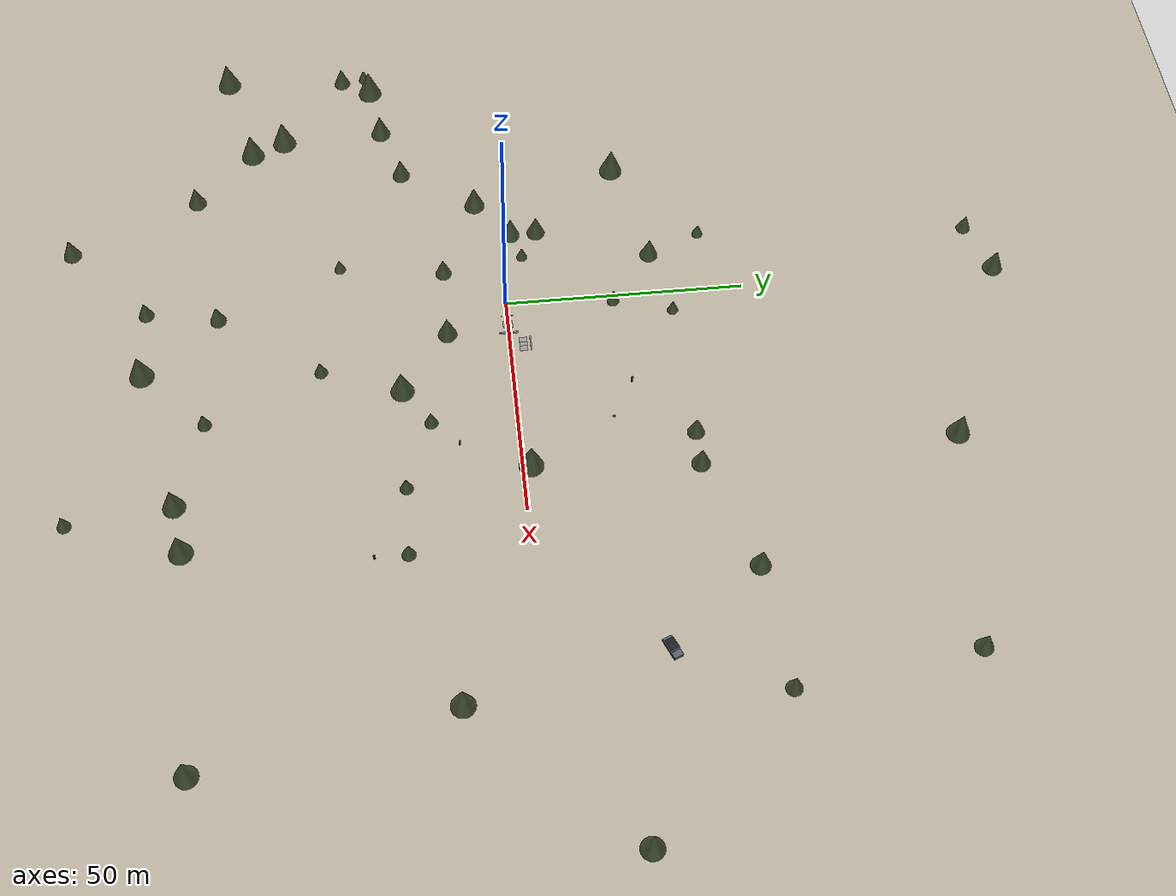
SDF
<?xml version="1.0"?>
<!-- GENERATED by hexabot_gazebo/scripts/generate_world.py from sim/course.json -->
<sdf version="1.9">
  <world name="scout_range_night">
    <physics name="2ms" type="dart">
      <max_step_size>0.002</max_step_size>
      <real_time_factor>1.0</real_time_factor>
    </physics>
    <plugin filename="gz-sim-physics-system" name="gz::sim::systems::Physics"/>
    <plugin filename="gz-sim-user-commands-system" name="gz::sim::systems::UserCommands"/>
    <plugin filename="gz-sim-scene-broadcaster-system" name="gz::sim::systems::SceneBroadcaster"/>
    <plugin filename="gz-sim-sensors-system" name="gz::sim::systems::Sensors">
      <render_engine>ogre2</render_engine>
    </plugin>
    <plugin filename="gz-sim-imu-system" name="gz::sim::systems::Imu"/>
    <plugin filename="gz-sim-navsat-system" name="gz::sim::systems::NavSat"/>
    <atmosphere type="adiabatic"><temperature>279</temperature><temperature_gradient>-0.0065</temperature_gradient></atmosphere>
    <!-- Set to your test site for meaningful GNSS coordinates. -->
    <spherical_coordinates>
      <surface_model>EARTH_WGS84</surface_model>
      <world_frame_orientation>ENU</world_frame_orientation>
      <latitude_deg>0.0</latitude_deg>
      <longitude_deg>0.0</longitude_deg>
      <elevation>0.0</elevation>
      <heading_deg>0</heading_deg>
    </spherical_coordinates>
    <scene><ambient>0.04 0.05 0.07 1</ambient><background>0.02 0.03 0.05 1</background><shadows>true</shadows></scene>
    <light type="directional" name="moon"><cast_shadows>false</cast_shadows><pose>0 0 30 0 0 0</pose><diffuse>0.06 0.07 0.11 1</diffuse><specular>0 0 0 1</specular><direction>0.3 0.4 -0.85</direction></light>
    <model name="ground">
      <static>true</static>
      <link name="link">
        <collision name="c"><geometry><plane><normal>0 0 1</normal><size>400 400</size></plane></geometry>
          <surface><friction><ode><mu>1.0</mu><mu2>1.0</mu2></ode></friction></surface></collision>
        <visual name="v"><geometry><plane><normal>0 0 1</normal><size>400 400</size></plane></geometry><material><ambient>0.72 0.69 0.62 1</ambient><diffuse>0.72 0.69 0.62 1</diffuse><specular>0.1 0.1 0.1 1</specular></material><plugin filename="gz-sim-thermal-system" name="gz::sim::systems::Thermal"><temperature>273.0</temperature></plugin></visual>
      </link>
    </model>

    <model name="rock_0">
      <static>true</static>
      <pose>1.1250 -0.2850 0.0125 0 0.00000 0.0000</pose>
      <link name="link">
        <collision name="c"><geometry><box><size>0.1500 0.1300 0.0250</size></box></geometry>
          <surface><friction><ode><mu>1.0</mu><mu2>1.0</mu2></ode></friction></surface></collision>
        <visual name="v"><geometry><box><size>0.1500 0.1300 0.0250</size></box></geometry><material><ambient>0.49 0.45 0.41 1</ambient><diffuse>0.49 0.45 0.41 1</diffuse><specular>0.1 0.1 0.1 1</specular></material><plugin filename="gz-sim-thermal-system" name="gz::sim::systems::Thermal"><temperature>281.0</temperature></plugin></visual>
      </link>
    </model>
    <model name="rock_1">
      <static>true</static>
      <pose>1.5100 0.2100 0.0175 0 0.00000 0.0000</pose>
      <link name="link">
        <collision name="c"><geometry><box><size>0.2200 0.1800 0.0350</size></box></geometry>
          <surface><friction><ode><mu>1.0</mu><mu2>1.0</mu2></ode></friction></surface></collision>
        <visual name="v"><geometry><box><size>0.2200 0.1800 0.0350</size></box></geometry><material><ambient>0.49 0.45 0.41 1</ambient><diffuse>0.49 0.45 0.41 1</diffuse><specular>0.1 0.1 0.1 1</specular></material><plugin filename="gz-sim-thermal-system" name="gz::sim::systems::Thermal"><temperature>281.0</temperature></plugin></visual>
      </link>
    </model>
    <model name="rock_2">
      <static>true</static>
      <pose>1.9150 -0.0500 0.0100 0 0.00000 0.0000</pose>
      <link name="link">
        <collision name="c"><geometry><box><size>0.1300 0.1400 0.0200</size></box></geometry>
          <surface><friction><ode><mu>1.0</mu><mu2>1.0</mu2></ode></friction></surface></collision>
        <visual name="v"><geometry><box><size>0.1300 0.1400 0.0200</size></box></geometry><material><ambient>0.49 0.45 0.41 1</ambient><diffuse>0.49 0.45 0.41 1</diffuse><specular>0.1 0.1 0.1 1</specular></material><plugin filename="gz-sim-thermal-system" name="gz::sim::systems::Thermal"><temperature>281.0</temperature></plugin></visual>
      </link>
    </model>
    <model name="rock_3">
      <static>true</static>
      <pose>2.2000 0.3600 0.0200 0 0.00000 0.0000</pose>
      <link name="link">
        <collision name="c"><geometry><box><size>0.2000 0.1600 0.0400</size></box></geometry>
          <surface><friction><ode><mu>1.0</mu><mu2>1.0</mu2></ode></friction></surface></collision>
        <visual name="v"><geometry><box><size>0.2000 0.1600 0.0400</size></box></geometry><material><ambient>0.49 0.45 0.41 1</ambient><diffuse>0.49 0.45 0.41 1</diffuse><specular>0.1 0.1 0.1 1</specular></material><plugin filename="gz-sim-thermal-system" name="gz::sim::systems::Thermal"><temperature>281.0</temperature></plugin></visual>
      </link>
    </model>
    <model name="rock_4">
      <static>true</static>
      <pose>2.3150 -0.3400 0.0150 0 0.00000 0.0000</pose>
      <link name="link">
        <collision name="c"><geometry><box><size>0.1300 0.1200 0.0300</size></box></geometry>
          <surface><friction><ode><mu>1.0</mu><mu2>1.0</mu2></ode></friction></surface></collision>
        <visual name="v"><geometry><box><size>0.1300 0.1200 0.0300</size></box></geometry><material><ambient>0.49 0.45 0.41 1</ambient><diffuse>0.49 0.45 0.41 1</diffuse><specular>0.1 0.1 0.1 1</specular></material><plugin filename="gz-sim-thermal-system" name="gz::sim::systems::Thermal"><temperature>281.0</temperature></plugin></visual>
      </link>
    </model>
    <model name="beam_5">
      <static>true</static>
      <pose>3.2600 0.0000 0.0300 0 0.00000 0.0000</pose>
      <link name="link">
        <collision name="c"><geometry><box><size>0.1200 2.4000 0.0600</size></box></geometry>
          <surface><friction><ode><mu>1.0</mu><mu2>1.0</mu2></ode></friction></surface></collision>
        <visual name="v"><geometry><box><size>0.1200 2.4000 0.0600</size></box></geometry><material><ambient>0.54 0.42 0.27 1</ambient><diffuse>0.54 0.42 0.27 1</diffuse><specular>0.1 0.1 0.1 1</specular></material><plugin filename="gz-sim-thermal-system" name="gz::sim::systems::Thermal"><temperature>281.0</temperature></plugin></visual>
      </link>
    </model>
    <model name="platform_6">
      <static>true</static>
      <pose>5.5000 0.0000 0.0250 0 0.00000 0.0000</pose>
      <link name="link">
        <collision name="c"><geometry><box><size>1.8000 2.0000 0.0500</size></box></geometry>
          <surface><friction><ode><mu>1.0</mu><mu2>1.0</mu2></ode></friction></surface></collision>
        <visual name="v"><geometry><box><size>1.8000 2.0000 0.0500</size></box></geometry><material><ambient>0.6 0.6 0.57 1</ambient><diffuse>0.6 0.6 0.57 1</diffuse><specular>0.1 0.1 0.1 1</specular></material><plugin filename="gz-sim-thermal-system" name="gz::sim::systems::Thermal"><temperature>281.0</temperature></plugin></visual>
      </link>
    </model>
    <model name="wall_7">
      <static>true</static>
      <pose>7.7250 0.0000 0.2250 0 0.00000 0.0000</pose>
      <link name="link">
        <collision name="c"><geometry><box><size>0.2500 4.0000 0.4500</size></box></geometry>
          <surface><friction><ode><mu>1.0</mu><mu2>1.0</mu2></ode></friction></surface></collision>
        <visual name="v"><geometry><box><size>0.2500 4.0000 0.4500</size></box></geometry><material><ambient>0.65 0.65 0.61 1</ambient><diffuse>0.65 0.65 0.61 1</diffuse><specular>0.1 0.1 0.1 1</specular></material><plugin filename="gz-sim-thermal-system" name="gz::sim::systems::Thermal"><temperature>281.0</temperature></plugin></visual>
      </link>
    </model>
    <model name="wall_8">
      <static>true</static>
      <pose>10.7000 4.3250 0.1500 0 0.00000 0.0000</pose>
      <link name="link">
        <collision name="c"><geometry><box><size>3.4000 0.2500 0.3000</size></box></geometry>
          <surface><friction><ode><mu>1.0</mu><mu2>1.0</mu2></ode></friction></surface></collision>
        <visual name="v"><geometry><box><size>3.4000 0.2500 0.3000</size></box></geometry><material><ambient>0.65 0.65 0.61 1</ambient><diffuse>0.65 0.65 0.61 1</diffuse><specular>0.1 0.1 0.1 1</specular></material><plugin filename="gz-sim-thermal-system" name="gz::sim::systems::Thermal"><temperature>281.0</temperature></plugin></visual>
      </link>
    </model>
    <model name="ramp_0">
      <static>true</static>
      <pose>9.6000 2.8000 0.0400 0 -0.08314 0.0000</pose>
      <link name="link">
        <collision name="c"><geometry><box><size>1.2042 1.6000 0.0200</size></box></geometry>
          <surface><friction><ode><mu>1.0</mu><mu2>1.0</mu2></ode></friction></surface></collision>
        <visual name="v"><geometry><box><size>1.2042 1.6000 0.0200</size></box></geometry><material><ambient>0.6 0.6 0.57 1</ambient><diffuse>0.6 0.6 0.57 1</diffuse><specular>0.1 0.1 0.1 1</specular></material><plugin filename="gz-sim-thermal-system" name="gz::sim::systems::Thermal"><temperature>281.0</temperature></plugin></visual>
      </link>
    </model>
    <model name="ramp_1">
      <static>true</static>
      <pose>10.7000 2.8000 0.0500 0 0.00000 0.0000</pose>
      <link name="link">
        <collision name="c"><geometry><box><size>1.0000 1.6000 0.1000</size></box></geometry>
          <surface><friction><ode><mu>1.0</mu><mu2>1.0</mu2></ode></friction></surface></collision>
        <visual name="v"><geometry><box><size>1.0000 1.6000 0.1000</size></box></geometry><material><ambient>0.6 0.6 0.57 1</ambient><diffuse>0.6 0.6 0.57 1</diffuse><specular>0.1 0.1 0.1 1</specular></material><plugin filename="gz-sim-thermal-system" name="gz::sim::systems::Thermal"><temperature>281.0</temperature></plugin></visual>
      </link>
    </model>
    <model name="ramp_2">
      <static>true</static>
      <pose>11.8000 2.8000 0.0400 0 0.08314 0.0000</pose>
      <link name="link">
        <collision name="c"><geometry><box><size>1.2042 1.6000 0.0200</size></box></geometry>
          <surface><friction><ode><mu>1.0</mu><mu2>1.0</mu2></ode></friction></surface></collision>
        <visual name="v"><geometry><box><size>1.2042 1.6000 0.0200</size></box></geometry><material><ambient>0.6 0.6 0.57 1</ambient><diffuse>0.6 0.6 0.57 1</diffuse><specular>0.1 0.1 0.1 1</specular></material><plugin filename="gz-sim-thermal-system" name="gz::sim::systems::Thermal"><temperature>281.0</temperature></plugin></visual>
      </link>
    </model>
    <model name="person_0">
      <static>true</static>
      <pose>34.00 -12.00 0 0 0 1.494</pose>
      <link name="link">
        <collision name="c"><pose>0 0 0.87 0 0 0</pose><geometry><cylinder><radius>0.22</radius><length>1.74</length></cylinder></geometry></collision>
        <visual name="legs"><pose>0 0 0.43 0 0 0</pose><geometry><box><size>0.22 0.32 0.86</size></box></geometry><material><ambient>0.17 0.18 0.2 1</ambient><diffuse>0.17 0.18 0.2 1</diffuse><specular>0.1 0.1 0.1 1</specular></material><plugin filename="gz-sim-thermal-system" name="gz::sim::systems::Thermal"><temperature>303.0</temperature></plugin></visual>
        <visual name="torso"><pose>0 0 1.17 0 0 0</pose><geometry><box><size>0.26 0.42 0.62</size></box></geometry><material><ambient>0.2901960784313726 0.35294117647058826 0.4470588235294118 1</ambient><diffuse>0.2901960784313726 0.35294117647058826 0.4470588235294118 1</diffuse><specular>0.1 0.1 0.1 1</specular></material><plugin filename="gz-sim-thermal-system" name="gz::sim::systems::Thermal"><temperature>305.0</temperature></plugin></visual>
        <visual name="head"><pose>0 0 1.6 0 0 0</pose><geometry><sphere><radius>0.11</radius></sphere></geometry><material><ambient>0.78 0.61 0.48 1</ambient><diffuse>0.78 0.61 0.48 1</diffuse><specular>0.1 0.1 0.1 1</specular></material><plugin filename="gz-sim-thermal-system" name="gz::sim::systems::Thermal"><temperature>309.0</temperature></plugin></visual>
      </link>
    </model>
    <model name="person_1">
      <static>true</static>
      <pose>22.00 24.00 0 0 0 0.785</pose>
      <link name="link">
        <collision name="c"><pose>0 0 0.87 0 0 0</pose><geometry><cylinder><radius>0.22</radius><length>1.74</length></cylinder></geometry></collision>
        <visual name="legs"><pose>0 0 0.43 0 0 0</pose><geometry><box><size>0.22 0.32 0.86</size></box></geometry><material><ambient>0.17 0.18 0.2 1</ambient><diffuse>0.17 0.18 0.2 1</diffuse><specular>0.1 0.1 0.1 1</specular></material><plugin filename="gz-sim-thermal-system" name="gz::sim::systems::Thermal"><temperature>303.0</temperature></plugin></visual>
        <visual name="torso"><pose>0 0 1.17 0 0 0</pose><geometry><box><size>0.26 0.42 0.62</size></box></geometry><material><ambient>0.5411764705882353 0.29411764705882354 0.22745098039215686 1</ambient><diffuse>0.5411764705882353 0.29411764705882354 0.22745098039215686 1</diffuse><specular>0.1 0.1 0.1 1</specular></material><plugin filename="gz-sim-thermal-system" name="gz::sim::systems::Thermal"><temperature>305.0</temperature></plugin></visual>
        <visual name="head"><pose>0 0 1.6 0 0 0</pose><geometry><sphere><radius>0.11</radius></sphere></geometry><material><ambient>0.78 0.61 0.48 1</ambient><diffuse>0.78 0.61 0.48 1</diffuse><specular>0.1 0.1 0.1 1</specular></material><plugin filename="gz-sim-thermal-system" name="gz::sim::systems::Thermal"><temperature>309.0</temperature></plugin></visual>
      </link>
    </model>
    <model name="person_2">
      <static>true</static>
      <pose>58.00 -30.00 0 0 0 0.785</pose>
      <link name="link">
        <collision name="c"><pose>0 0 0.87 0 0 0</pose><geometry><cylinder><radius>0.22</radius><length>1.74</length></cylinder></geometry></collision>
        <visual name="legs"><pose>0 0 0.43 0 0 0</pose><geometry><box><size>0.22 0.32 0.86</size></box></geometry><material><ambient>0.17 0.18 0.2 1</ambient><diffuse>0.17 0.18 0.2 1</diffuse><specular>0.1 0.1 0.1 1</specular></material><plugin filename="gz-sim-thermal-system" name="gz::sim::systems::Thermal"><temperature>303.0</temperature></plugin></visual>
        <visual name="torso"><pose>0 0 1.17 0 0 0</pose><geometry><box><size>0.26 0.42 0.62</size></box></geometry><material><ambient>0.37254901960784315 0.4196078431372549 0.23529411764705882 1</ambient><diffuse>0.37254901960784315 0.4196078431372549 0.23529411764705882 1</diffuse><specular>0.1 0.1 0.1 1</specular></material><plugin filename="gz-sim-thermal-system" name="gz::sim::systems::Thermal"><temperature>305.0</temperature></plugin></visual>
        <visual name="head"><pose>0 0 1.6 0 0 0</pose><geometry><sphere><radius>0.11</radius></sphere></geometry><material><ambient>0.78 0.61 0.48 1</ambient><diffuse>0.78 0.61 0.48 1</diffuse><specular>0.1 0.1 0.1 1</specular></material><plugin filename="gz-sim-thermal-system" name="gz::sim::systems::Thermal"><temperature>309.0</temperature></plugin></visual>
      </link>
    </model>
    <model name="drone">
      <static>true</static>
      <pose>45.31 16.55 24.0 0 0 2.071</pose>
      <link name="link">
        <collision name="c"><geometry><box><size>0.5 0.5 0.12</size></box></geometry></collision>
        <visual name="body"><geometry><box><size>0.22 0.14 0.08</size></box></geometry><material><ambient>0.16 0.17 0.19 1</ambient><diffuse>0.16 0.17 0.19 1</diffuse><specular>0.1 0.1 0.1 1</specular></material><plugin filename="gz-sim-thermal-system" name="gz::sim::systems::Thermal"><temperature>306.0</temperature></plugin></visual>
        <visual name="arms"><geometry><box><size>0.42 0.03 0.02</size></box></geometry><material><ambient>0.16 0.17 0.19 1</ambient><diffuse>0.16 0.17 0.19 1</diffuse><specular>0.1 0.1 0.1 1</specular></material><plugin filename="gz-sim-thermal-system" name="gz::sim::systems::Thermal"><temperature>300.0</temperature></plugin></visual>
        <visual name="rotor0"><pose>0.141 0.141 0.03 0 0 0</pose><geometry><cylinder><radius>0.1</radius><length>0.01</length></cylinder></geometry><material><ambient>0.6 0.62 0.65 1</ambient><diffuse>0.6 0.62 0.65 1</diffuse><specular>0.1 0.1 0.1 1</specular></material><plugin filename="gz-sim-thermal-system" name="gz::sim::systems::Thermal"><temperature>318.0</temperature></plugin></visual><visual name="rotor1"><pose>-0.141 0.141 0.03 0 0 0</pose><geometry><cylinder><radius>0.1</radius><length>0.01</length></cylinder></geometry><material><ambient>0.6 0.62 0.65 1</ambient><diffuse>0.6 0.62 0.65 1</diffuse><specular>0.1 0.1 0.1 1</specular></material><plugin filename="gz-sim-thermal-system" name="gz::sim::systems::Thermal"><temperature>318.0</temperature></plugin></visual><visual name="rotor2"><pose>-0.141 -0.141 0.03 0 0 0</pose><geometry><cylinder><radius>0.1</radius><length>0.01</length></cylinder></geometry><material><ambient>0.6 0.62 0.65 1</ambient><diffuse>0.6 0.62 0.65 1</diffuse><specular>0.1 0.1 0.1 1</specular></material><plugin filename="gz-sim-thermal-system" name="gz::sim::systems::Thermal"><temperature>318.0</temperature></plugin></visual><visual name="rotor3"><pose>0.141 -0.141 0.03 0 0 0</pose><geometry><cylinder><radius>0.1</radius><length>0.01</length></cylinder></geometry><material><ambient>0.6 0.62 0.65 1</ambient><diffuse>0.6 0.62 0.65 1</diffuse><specular>0.1 0.1 0.1 1</specular></material><plugin filename="gz-sim-thermal-system" name="gz::sim::systems::Thermal"><temperature>318.0</temperature></plugin></visual>
      </link>
    </model>
    <model name="vehicle">
      <static>true</static>
      <pose>82 24 0 0 0 0.4</pose>
      <link name="link">
        <collision name="c"><pose>0 0 0.9 0 0 0</pose><geometry><box><size>4.5 1.9 1.8</size></box></geometry></collision>
        <visual name="body"><pose>0 0 0.78 0 0 0</pose><geometry><box><size>4.5 1.9 0.75</size></box></geometry><material><ambient>0.33 0.38 0.42 1</ambient><diffuse>0.33 0.38 0.42 1</diffuse><specular>0.1 0.1 0.1 1</specular></material><plugin filename="gz-sim-thermal-system" name="gz::sim::systems::Thermal"><temperature>289.0</temperature></plugin></visual>
        <visual name="engine"><pose>1.55 0 0.8 0 0 0</pose><geometry><box><size>1.4 1.86 0.6</size></box></geometry><material><ambient>0.33 0.38 0.42 1</ambient><diffuse>0.33 0.38 0.42 1</diffuse><specular>0.1 0.1 0.1 1</specular></material><plugin filename="gz-sim-thermal-system" name="gz::sim::systems::Thermal"><temperature>333.0</temperature></plugin></visual>
        <visual name="cabin"><pose>-0.3 0 1.45 0 0 0</pose><geometry><box><size>2.5 1.75 0.6</size></box></geometry><material><ambient>0.1 0.13 0.16 1</ambient><diffuse>0.1 0.13 0.16 1</diffuse><specular>0.1 0.1 0.1 1</specular></material><plugin filename="gz-sim-thermal-system" name="gz::sim::systems::Thermal"><temperature>287.0</temperature></plugin></visual>
      </link>
    </model>
    <model name="tree_0">
      <static>true</static>
      <pose>41.52 1.59 0 0 0 0</pose>
      <link name="link">
        <collision name="c"><pose>0 0 4.44 0 0 0</pose><geometry><cylinder><radius>0.53</radius><length>8.88</length></cylinder></geometry></collision>
        <visual name="trunk"><pose>0 0 1.95 0 0 0</pose><geometry><cylinder><radius>0.18</radius><length>4.00</length></cylinder></geometry><material><ambient>0.36 0.28 0.2 1</ambient><diffuse>0.36 0.28 0.2 1</diffuse><specular>0.1 0.1 0.1 1</specular></material><plugin filename="gz-sim-thermal-system" name="gz::sim::systems::Thermal"><temperature>284.0</temperature></plugin></visual>
        <visual name="crown"><pose>0 0 5.51 0 0 0</pose><geometry><cone><radius>2.49</radius><length>6.66</length></cone></geometry><material><ambient>0.33 0.4 0.25 1</ambient><diffuse>0.33 0.4 0.25 1</diffuse><specular>0.1 0.1 0.1 1</specular></material><plugin filename="gz-sim-thermal-system" name="gz::sim::systems::Thermal"><temperature>283.0</temperature></plugin></visual>
      </link>
    </model>
    <model name="tree_1">
      <static>true</static>
      <pose>0.19 -59.73 0 0 0 0</pose>
      <link name="link">
        <collision name="c"><pose>0 0 3.01 0 0 0</pose><geometry><cylinder><radius>0.36</radius><length>6.03</length></cylinder></geometry></collision>
        <visual name="trunk"><pose>0 0 1.33 0 0 0</pose><geometry><cylinder><radius>0.18</radius><length>2.71</length></cylinder></geometry><material><ambient>0.36 0.28 0.2 1</ambient><diffuse>0.36 0.28 0.2 1</diffuse><specular>0.1 0.1 0.1 1</specular></material><plugin filename="gz-sim-thermal-system" name="gz::sim::systems::Thermal"><temperature>284.0</temperature></plugin></visual>
        <visual name="crown"><pose>0 0 3.74 0 0 0</pose><geometry><cone><radius>1.69</radius><length>4.52</length></cone></geometry><material><ambient>0.33 0.4 0.25 1</ambient><diffuse>0.33 0.4 0.25 1</diffuse><specular>0.1 0.1 0.1 1</specular></material><plugin filename="gz-sim-thermal-system" name="gz::sim::systems::Thermal"><temperature>283.0</temperature></plugin></visual>
      </link>
    </model>
    <model name="tree_2">
      <static>true</static>
      <pose>-16.75 7.92 0 0 0 0</pose>
      <link name="link">
        <collision name="c"><pose>0 0 3.38 0 0 0</pose><geometry><cylinder><radius>0.41</radius><length>6.77</length></cylinder></geometry></collision>
        <visual name="trunk"><pose>0 0 1.49 0 0 0</pose><geometry><cylinder><radius>0.18</radius><length>3.04</length></cylinder></geometry><material><ambient>0.36 0.28 0.2 1</ambient><diffuse>0.36 0.28 0.2 1</diffuse><specular>0.1 0.1 0.1 1</specular></material><plugin filename="gz-sim-thermal-system" name="gz::sim::systems::Thermal"><temperature>284.0</temperature></plugin></visual>
        <visual name="crown"><pose>0 0 4.20 0 0 0</pose><geometry><cone><radius>1.89</radius><length>5.07</length></cone></geometry><material><ambient>0.33 0.4 0.25 1</ambient><diffuse>0.33 0.4 0.25 1</diffuse><specular>0.1 0.1 0.1 1</specular></material><plugin filename="gz-sim-thermal-system" name="gz::sim::systems::Thermal"><temperature>283.0</temperature></plugin></visual>
      </link>
    </model>
    <model name="tree_3">
      <static>true</static>
      <pose>15.04 -38.89 0 0 0 0</pose>
      <link name="link">
        <collision name="c"><pose>0 0 2.39 0 0 0</pose><geometry><cylinder><radius>0.29</radius><length>4.78</length></cylinder></geometry></collision>
        <visual name="trunk"><pose>0 0 1.05 0 0 0</pose><geometry><cylinder><radius>0.18</radius><length>2.15</length></cylinder></geometry><material><ambient>0.36 0.28 0.2 1</ambient><diffuse>0.36 0.28 0.2 1</diffuse><specular>0.1 0.1 0.1 1</specular></material><plugin filename="gz-sim-thermal-system" name="gz::sim::systems::Thermal"><temperature>284.0</temperature></plugin></visual>
        <visual name="crown"><pose>0 0 2.96 0 0 0</pose><geometry><cone><radius>1.34</radius><length>3.58</length></cone></geometry><material><ambient>0.33 0.4 0.25 1</ambient><diffuse>0.33 0.4 0.25 1</diffuse><specular>0.1 0.1 0.1 1</specular></material><plugin filename="gz-sim-thermal-system" name="gz::sim::systems::Thermal"><temperature>283.0</temperature></plugin></visual>
      </link>
    </model>
    <model name="tree_4">
      <static>true</static>
      <pose>25.54 -62.41 0 0 0 0</pose>
      <link name="link">
        <collision name="c"><pose>0 0 2.49 0 0 0</pose><geometry><cylinder><radius>0.30</radius><length>4.99</length></cylinder></geometry></collision>
        <visual name="trunk"><pose>0 0 1.10 0 0 0</pose><geometry><cylinder><radius>0.18</radius><length>2.24</length></cylinder></geometry><material><ambient>0.36 0.28 0.2 1</ambient><diffuse>0.36 0.28 0.2 1</diffuse><specular>0.1 0.1 0.1 1</specular></material><plugin filename="gz-sim-thermal-system" name="gz::sim::systems::Thermal"><temperature>284.0</temperature></plugin></visual>
        <visual name="crown"><pose>0 0 3.09 0 0 0</pose><geometry><cone><radius>1.40</radius><length>3.74</length></cone></geometry><material><ambient>0.33 0.4 0.25 1</ambient><diffuse>0.33 0.4 0.25 1</diffuse><specular>0.1 0.1 0.1 1</specular></material><plugin filename="gz-sim-thermal-system" name="gz::sim::systems::Thermal"><temperature>283.0</temperature></plugin></visual>
      </link>
    </model>
    <model name="tree_5">
      <static>true</static>
      <pose>-8.62 31.27 0 0 0 0</pose>
      <link name="link">
        <collision name="c"><pose>0 0 3.34 0 0 0</pose><geometry><cylinder><radius>0.40</radius><length>6.67</length></cylinder></geometry></collision>
        <visual name="trunk"><pose>0 0 1.47 0 0 0</pose><geometry><cylinder><radius>0.18</radius><length>3.00</length></cylinder></geometry><material><ambient>0.36 0.28 0.2 1</ambient><diffuse>0.36 0.28 0.2 1</diffuse><specular>0.1 0.1 0.1 1</specular></material><plugin filename="gz-sim-thermal-system" name="gz::sim::systems::Thermal"><temperature>284.0</temperature></plugin></visual>
        <visual name="crown"><pose>0 0 4.14 0 0 0</pose><geometry><cone><radius>1.87</radius><length>5.01</length></cone></geometry><material><ambient>0.33 0.4 0.25 1</ambient><diffuse>0.33 0.4 0.25 1</diffuse><specular>0.1 0.1 0.1 1</specular></material><plugin filename="gz-sim-thermal-system" name="gz::sim::systems::Thermal"><temperature>283.0</temperature></plugin></visual>
      </link>
    </model>
    <model name="tree_6">
      <static>true</static>
      <pose>-9.85 99.64 0 0 0 0</pose>
      <link name="link">
        <collision name="c"><pose>0 0 2.62 0 0 0</pose><geometry><cylinder><radius>0.31</radius><length>5.24</length></cylinder></geometry></collision>
        <visual name="trunk"><pose>0 0 1.15 0 0 0</pose><geometry><cylinder><radius>0.18</radius><length>2.36</length></cylinder></geometry><material><ambient>0.36 0.28 0.2 1</ambient><diffuse>0.36 0.28 0.2 1</diffuse><specular>0.1 0.1 0.1 1</specular></material><plugin filename="gz-sim-thermal-system" name="gz::sim::systems::Thermal"><temperature>284.0</temperature></plugin></visual>
        <visual name="crown"><pose>0 0 3.25 0 0 0</pose><geometry><cone><radius>1.47</radius><length>3.93</length></cone></geometry><material><ambient>0.33 0.4 0.25 1</ambient><diffuse>0.33 0.4 0.25 1</diffuse><specular>0.1 0.1 0.1 1</specular></material><plugin filename="gz-sim-thermal-system" name="gz::sim::systems::Thermal"><temperature>283.0</temperature></plugin></visual>
      </link>
    </model>
    <model name="tree_7">
      <static>true</static>
      <pose>43.86 -23.04 0 0 0 0</pose>
      <link name="link">
        <collision name="c"><pose>0 0 2.36 0 0 0</pose><geometry><cylinder><radius>0.28</radius><length>4.72</length></cylinder></geometry></collision>
        <visual name="trunk"><pose>0 0 1.04 0 0 0</pose><geometry><cylinder><radius>0.18</radius><length>2.12</length></cylinder></geometry><material><ambient>0.36 0.28 0.2 1</ambient><diffuse>0.36 0.28 0.2 1</diffuse><specular>0.1 0.1 0.1 1</specular></material><plugin filename="gz-sim-thermal-system" name="gz::sim::systems::Thermal"><temperature>284.0</temperature></plugin></visual>
        <visual name="crown"><pose>0 0 2.93 0 0 0</pose><geometry><cone><radius>1.32</radius><length>3.54</length></cone></geometry><material><ambient>0.33 0.4 0.25 1</ambient><diffuse>0.33 0.4 0.25 1</diffuse><specular>0.1 0.1 0.1 1</specular></material><plugin filename="gz-sim-thermal-system" name="gz::sim::systems::Thermal"><temperature>283.0</temperature></plugin></visual>
      </link>
    </model>
    <model name="tree_8">
      <static>true</static>
      <pose>43.79 34.84 0 0 0 0</pose>
      <link name="link">
        <collision name="c"><pose>0 0 3.37 0 0 0</pose><geometry><cylinder><radius>0.40</radius><length>6.74</length></cylinder></geometry></collision>
        <visual name="trunk"><pose>0 0 1.48 0 0 0</pose><geometry><cylinder><radius>0.18</radius><length>3.03</length></cylinder></geometry><material><ambient>0.36 0.28 0.2 1</ambient><diffuse>0.36 0.28 0.2 1</diffuse><specular>0.1 0.1 0.1 1</specular></material><plugin filename="gz-sim-thermal-system" name="gz::sim::systems::Thermal"><temperature>284.0</temperature></plugin></visual>
        <visual name="crown"><pose>0 0 4.18 0 0 0</pose><geometry><cone><radius>1.89</radius><length>5.05</length></cone></geometry><material><ambient>0.33 0.4 0.25 1</ambient><diffuse>0.33 0.4 0.25 1</diffuse><specular>0.1 0.1 0.1 1</specular></material><plugin filename="gz-sim-thermal-system" name="gz::sim::systems::Thermal"><temperature>283.0</temperature></plugin></visual>
      </link>
    </model>
    <model name="tree_9">
      <static>true</static>
      <pose>21.69 -22.64 0 0 0 0</pose>
      <link name="link">
        <collision name="c"><pose>0 0 4.28 0 0 0</pose><geometry><cylinder><radius>0.51</radius><length>8.56</length></cylinder></geometry></collision>
        <visual name="trunk"><pose>0 0 1.88 0 0 0</pose><geometry><cylinder><radius>0.18</radius><length>3.85</length></cylinder></geometry><material><ambient>0.36 0.28 0.2 1</ambient><diffuse>0.36 0.28 0.2 1</diffuse><specular>0.1 0.1 0.1 1</specular></material><plugin filename="gz-sim-thermal-system" name="gz::sim::systems::Thermal"><temperature>284.0</temperature></plugin></visual>
        <visual name="crown"><pose>0 0 5.31 0 0 0</pose><geometry><cone><radius>2.40</radius><length>6.42</length></cone></geometry><material><ambient>0.33 0.4 0.25 1</ambient><diffuse>0.33 0.4 0.25 1</diffuse><specular>0.1 0.1 0.1 1</specular></material><plugin filename="gz-sim-thermal-system" name="gz::sim::systems::Thermal"><temperature>283.0</temperature></plugin></visual>
      </link>
    </model>
    <model name="tree_10">
      <static>true</static>
      <pose>-47.89 -23.82 0 0 0 0</pose>
      <link name="link">
        <collision name="c"><pose>0 0 3.70 0 0 0</pose><geometry><cylinder><radius>0.44</radius><length>7.40</length></cylinder></geometry></collision>
        <visual name="trunk"><pose>0 0 1.63 0 0 0</pose><geometry><cylinder><radius>0.18</radius><length>3.33</length></cylinder></geometry><material><ambient>0.36 0.28 0.2 1</ambient><diffuse>0.36 0.28 0.2 1</diffuse><specular>0.1 0.1 0.1 1</specular></material><plugin filename="gz-sim-thermal-system" name="gz::sim::systems::Thermal"><temperature>284.0</temperature></plugin></visual>
        <visual name="crown"><pose>0 0 4.59 0 0 0</pose><geometry><cone><radius>2.07</radius><length>5.55</length></cone></geometry><material><ambient>0.33 0.4 0.25 1</ambient><diffuse>0.33 0.4 0.25 1</diffuse><specular>0.1 0.1 0.1 1</specular></material><plugin filename="gz-sim-thermal-system" name="gz::sim::systems::Thermal"><temperature>283.0</temperature></plugin></visual>
      </link>
    </model>
    <model name="tree_11">
      <static>true</static>
      <pose>90.55 -15.31 0 0 0 0</pose>
      <link name="link">
        <collision name="c"><pose>0 0 4.30 0 0 0</pose><geometry><cylinder><radius>0.52</radius><length>8.61</length></cylinder></geometry></collision>
        <visual name="trunk"><pose>0 0 1.89 0 0 0</pose><geometry><cylinder><radius>0.18</radius><length>3.87</length></cylinder></geometry><material><ambient>0.36 0.28 0.2 1</ambient><diffuse>0.36 0.28 0.2 1</diffuse><specular>0.1 0.1 0.1 1</specular></material><plugin filename="gz-sim-thermal-system" name="gz::sim::systems::Thermal"><temperature>284.0</temperature></plugin></visual>
        <visual name="crown"><pose>0 0 5.34 0 0 0</pose><geometry><cone><radius>2.41</radius><length>6.45</length></cone></geometry><material><ambient>0.33 0.4 0.25 1</ambient><diffuse>0.33 0.4 0.25 1</diffuse><specular>0.1 0.1 0.1 1</specular></material><plugin filename="gz-sim-thermal-system" name="gz::sim::systems::Thermal"><temperature>283.0</temperature></plugin></visual>
      </link>
    </model>
    <model name="tree_12">
      <static>true</static>
      <pose>29.18 -17.31 0 0 0 0</pose>
      <link name="link">
        <collision name="c"><pose>0 0 2.44 0 0 0</pose><geometry><cylinder><radius>0.29</radius><length>4.87</length></cylinder></geometry></collision>
        <visual name="trunk"><pose>0 0 1.07 0 0 0</pose><geometry><cylinder><radius>0.18</radius><length>2.19</length></cylinder></geometry><material><ambient>0.36 0.28 0.2 1</ambient><diffuse>0.36 0.28 0.2 1</diffuse><specular>0.1 0.1 0.1 1</specular></material><plugin filename="gz-sim-thermal-system" name="gz::sim::systems::Thermal"><temperature>284.0</temperature></plugin></visual>
        <visual name="crown"><pose>0 0 3.02 0 0 0</pose><geometry><cone><radius>1.36</radius><length>3.66</length></cone></geometry><material><ambient>0.33 0.4 0.25 1</ambient><diffuse>0.33 0.4 0.25 1</diffuse><specular>0.1 0.1 0.1 1</specular></material><plugin filename="gz-sim-thermal-system" name="gz::sim::systems::Thermal"><temperature>283.0</temperature></plugin></visual>
      </link>
    </model>
    <model name="tree_13">
      <static>true</static>
      <pose>-13.80 42.47 0 0 0 0</pose>
      <link name="link">
        <collision name="c"><pose>0 0 2.05 0 0 0</pose><geometry><cylinder><radius>0.25</radius><length>4.10</length></cylinder></geometry></collision>
        <visual name="trunk"><pose>0 0 0.90 0 0 0</pose><geometry><cylinder><radius>0.18</radius><length>1.85</length></cylinder></geometry><material><ambient>0.36 0.28 0.2 1</ambient><diffuse>0.36 0.28 0.2 1</diffuse><specular>0.1 0.1 0.1 1</specular></material><plugin filename="gz-sim-thermal-system" name="gz::sim::systems::Thermal"><temperature>284.0</temperature></plugin></visual>
        <visual name="crown"><pose>0 0 2.54 0 0 0</pose><geometry><cone><radius>1.15</radius><length>3.08</length></cone></geometry><material><ambient>0.33 0.4 0.25 1</ambient><diffuse>0.33 0.4 0.25 1</diffuse><specular>0.1 0.1 0.1 1</specular></material><plugin filename="gz-sim-thermal-system" name="gz::sim::systems::Thermal"><temperature>283.0</temperature></plugin></visual>
      </link>
    </model>
    <model name="tree_14">
      <static>true</static>
      <pose>92.41 44.75 0 0 0 0</pose>
      <link name="link">
        <collision name="c"><pose>0 0 2.92 0 0 0</pose><geometry><cylinder><radius>0.35</radius><length>5.84</length></cylinder></geometry></collision>
        <visual name="trunk"><pose>0 0 1.29 0 0 0</pose><geometry><cylinder><radius>0.18</radius><length>2.63</length></cylinder></geometry><material><ambient>0.36 0.28 0.2 1</ambient><diffuse>0.36 0.28 0.2 1</diffuse><specular>0.1 0.1 0.1 1</specular></material><plugin filename="gz-sim-thermal-system" name="gz::sim::systems::Thermal"><temperature>284.0</temperature></plugin></visual>
        <visual name="crown"><pose>0 0 3.62 0 0 0</pose><geometry><cone><radius>1.64</radius><length>4.38</length></cone></geometry><material><ambient>0.33 0.4 0.25 1</ambient><diffuse>0.33 0.4 0.25 1</diffuse><specular>0.1 0.1 0.1 1</specular></material><plugin filename="gz-sim-thermal-system" name="gz::sim::systems::Thermal"><temperature>283.0</temperature></plugin></visual>
      </link>
    </model>
    <model name="tree_15">
      <static>true</static>
      <pose>-32.12 25.85 0 0 0 0</pose>
      <link name="link">
        <collision name="c"><pose>0 0 4.37 0 0 0</pose><geometry><cylinder><radius>0.52</radius><length>8.73</length></cylinder></geometry></collision>
        <visual name="trunk"><pose>0 0 1.92 0 0 0</pose><geometry><cylinder><radius>0.18</radius><length>3.93</length></cylinder></geometry><material><ambient>0.36 0.28 0.2 1</ambient><diffuse>0.36 0.28 0.2 1</diffuse><specular>0.1 0.1 0.1 1</specular></material><plugin filename="gz-sim-thermal-system" name="gz::sim::systems::Thermal"><temperature>284.0</temperature></plugin></visual>
        <visual name="crown"><pose>0 0 5.41 0 0 0</pose><geometry><cone><radius>2.44</radius><length>6.55</length></cone></geometry><material><ambient>0.33 0.4 0.25 1</ambient><diffuse>0.33 0.4 0.25 1</diffuse><specular>0.1 0.1 0.1 1</specular></material><plugin filename="gz-sim-thermal-system" name="gz::sim::systems::Thermal"><temperature>283.0</temperature></plugin></visual>
      </link>
    </model>
    <model name="tree_16">
      <static>true</static>
      <pose>-2.55 -74.61 0 0 0 0</pose>
      <link name="link">
        <collision name="c"><pose>0 0 2.83 0 0 0</pose><geometry><cylinder><radius>0.34</radius><length>5.65</length></cylinder></geometry></collision>
        <visual name="trunk"><pose>0 0 1.24 0 0 0</pose><geometry><cylinder><radius>0.18</radius><length>2.54</length></cylinder></geometry><material><ambient>0.36 0.28 0.2 1</ambient><diffuse>0.36 0.28 0.2 1</diffuse><specular>0.1 0.1 0.1 1</specular></material><plugin filename="gz-sim-thermal-system" name="gz::sim::systems::Thermal"><temperature>284.0</temperature></plugin></visual>
        <visual name="crown"><pose>0 0 3.51 0 0 0</pose><geometry><cone><radius>1.58</radius><length>4.24</length></cone></geometry><material><ambient>0.33 0.4 0.25 1</ambient><diffuse>0.33 0.4 0.25 1</diffuse><specular>0.1 0.1 0.1 1</specular></material><plugin filename="gz-sim-thermal-system" name="gz::sim::systems::Thermal"><temperature>283.0</temperature></plugin></visual>
      </link>
    </model>
    <model name="tree_17">
      <static>true</static>
      <pose>2.35 22.37 0 0 0 0</pose>
      <link name="link">
        <collision name="c"><pose>0 0 2.33 0 0 0</pose><geometry><cylinder><radius>0.28</radius><length>4.67</length></cylinder></geometry></collision>
        <visual name="trunk"><pose>0 0 1.03 0 0 0</pose><geometry><cylinder><radius>0.18</radius><length>2.10</length></cylinder></geometry><material><ambient>0.36 0.28 0.2 1</ambient><diffuse>0.36 0.28 0.2 1</diffuse><specular>0.1 0.1 0.1 1</specular></material><plugin filename="gz-sim-thermal-system" name="gz::sim::systems::Thermal"><temperature>284.0</temperature></plugin></visual>
        <visual name="crown"><pose>0 0 2.89 0 0 0</pose><geometry><cone><radius>1.31</radius><length>3.50</length></cone></geometry><material><ambient>0.33 0.4 0.25 1</ambient><diffuse>0.33 0.4 0.25 1</diffuse><specular>0.1 0.1 0.1 1</specular></material><plugin filename="gz-sim-thermal-system" name="gz::sim::systems::Thermal"><temperature>283.0</temperature></plugin></visual>
      </link>
    </model>
    <model name="tree_18">
      <static>true</static>
      <pose>58.46 -23.39 0 0 0 0</pose>
      <link name="link">
        <collision name="c"><pose>0 0 2.48 0 0 0</pose><geometry><cylinder><radius>0.30</radius><length>4.95</length></cylinder></geometry></collision>
        <visual name="trunk"><pose>0 0 1.09 0 0 0</pose><geometry><cylinder><radius>0.18</radius><length>2.23</length></cylinder></geometry><material><ambient>0.36 0.28 0.2 1</ambient><diffuse>0.36 0.28 0.2 1</diffuse><specular>0.1 0.1 0.1 1</specular></material><plugin filename="gz-sim-thermal-system" name="gz::sim::systems::Thermal"><temperature>284.0</temperature></plugin></visual>
        <visual name="crown"><pose>0 0 3.07 0 0 0</pose><geometry><cone><radius>1.39</radius><length>3.71</length></cone></geometry><material><ambient>0.33 0.4 0.25 1</ambient><diffuse>0.33 0.4 0.25 1</diffuse><specular>0.1 0.1 0.1 1</specular></material><plugin filename="gz-sim-thermal-system" name="gz::sim::systems::Thermal"><temperature>283.0</temperature></plugin></visual>
      </link>
    </model>
    <model name="tree_19">
      <static>true</static>
      <pose>-11.23 -34.19 0 0 0 0</pose>
      <link name="link">
        <collision name="c"><pose>0 0 2.11 0 0 0</pose><geometry><cylinder><radius>0.25</radius><length>4.22</length></cylinder></geometry></collision>
        <visual name="trunk"><pose>0 0 0.93 0 0 0</pose><geometry><cylinder><radius>0.18</radius><length>1.90</length></cylinder></geometry><material><ambient>0.36 0.28 0.2 1</ambient><diffuse>0.36 0.28 0.2 1</diffuse><specular>0.1 0.1 0.1 1</specular></material><plugin filename="gz-sim-thermal-system" name="gz::sim::systems::Thermal"><temperature>284.0</temperature></plugin></visual>
        <visual name="crown"><pose>0 0 2.62 0 0 0</pose><geometry><cone><radius>1.18</radius><length>3.16</length></cone></geometry><material><ambient>0.33 0.4 0.25 1</ambient><diffuse>0.33 0.4 0.25 1</diffuse><specular>0.1 0.1 0.1 1</specular></material><plugin filename="gz-sim-thermal-system" name="gz::sim::systems::Thermal"><temperature>283.0</temperature></plugin></visual>
      </link>
    </model>
    <model name="tree_20">
      <static>true</static>
      <pose>-19.71 -90.60 0 0 0 0</pose>
      <link name="link">
        <collision name="c"><pose>0 0 3.37 0 0 0</pose><geometry><cylinder><radius>0.40</radius><length>6.74</length></cylinder></geometry></collision>
        <visual name="trunk"><pose>0 0 1.48 0 0 0</pose><geometry><cylinder><radius>0.18</radius><length>3.03</length></cylinder></geometry><material><ambient>0.36 0.28 0.2 1</ambient><diffuse>0.36 0.28 0.2 1</diffuse><specular>0.1 0.1 0.1 1</specular></material><plugin filename="gz-sim-thermal-system" name="gz::sim::systems::Thermal"><temperature>284.0</temperature></plugin></visual>
        <visual name="crown"><pose>0 0 4.18 0 0 0</pose><geometry><cone><radius>1.89</radius><length>5.05</length></cone></geometry><material><ambient>0.33 0.4 0.25 1</ambient><diffuse>0.33 0.4 0.25 1</diffuse><specular>0.1 0.1 0.1 1</specular></material><plugin filename="gz-sim-thermal-system" name="gz::sim::systems::Thermal"><temperature>283.0</temperature></plugin></visual>
      </link>
    </model>
    <model name="tree_21">
      <static>true</static>
      <pose>54.70 -66.46 0 0 0 0</pose>
      <link name="link">
        <collision name="c"><pose>0 0 4.30 0 0 0</pose><geometry><cylinder><radius>0.52</radius><length>8.60</length></cylinder></geometry></collision>
        <visual name="trunk"><pose>0 0 1.89 0 0 0</pose><geometry><cylinder><radius>0.18</radius><length>3.87</length></cylinder></geometry><material><ambient>0.36 0.28 0.2 1</ambient><diffuse>0.36 0.28 0.2 1</diffuse><specular>0.1 0.1 0.1 1</specular></material><plugin filename="gz-sim-thermal-system" name="gz::sim::systems::Thermal"><temperature>284.0</temperature></plugin></visual>
        <visual name="crown"><pose>0 0 5.33 0 0 0</pose><geometry><cone><radius>2.41</radius><length>6.45</length></cone></geometry><material><ambient>0.33 0.4 0.25 1</ambient><diffuse>0.33 0.4 0.25 1</diffuse><specular>0.1 0.1 0.1 1</specular></material><plugin filename="gz-sim-thermal-system" name="gz::sim::systems::Thermal"><temperature>283.0</temperature></plugin></visual>
      </link>
    </model>
    <model name="tree_22">
      <static>true</static>
      <pose>67.23 42.73 0 0 0 0</pose>
      <link name="link">
        <collision name="c"><pose>0 0 3.62 0 0 0</pose><geometry><cylinder><radius>0.43</radius><length>7.25</length></cylinder></geometry></collision>
        <visual name="trunk"><pose>0 0 1.59 0 0 0</pose><geometry><cylinder><radius>0.18</radius><length>3.26</length></cylinder></geometry><material><ambient>0.36 0.28 0.2 1</ambient><diffuse>0.36 0.28 0.2 1</diffuse><specular>0.1 0.1 0.1 1</specular></material><plugin filename="gz-sim-thermal-system" name="gz::sim::systems::Thermal"><temperature>284.0</temperature></plugin></visual>
        <visual name="crown"><pose>0 0 4.49 0 0 0</pose><geometry><cone><radius>2.03</radius><length>5.43</length></cone></geometry><material><ambient>0.33 0.4 0.25 1</ambient><diffuse>0.33 0.4 0.25 1</diffuse><specular>0.1 0.1 0.1 1</specular></material><plugin filename="gz-sim-thermal-system" name="gz::sim::systems::Thermal"><temperature>283.0</temperature></plugin></visual>
      </link>
    </model>
    <model name="tree_23">
      <static>true</static>
      <pose>99.37 -64.77 0 0 0 0</pose>
      <link name="link">
        <collision name="c"><pose>0 0 4.09 0 0 0</pose><geometry><cylinder><radius>0.49</radius><length>8.19</length></cylinder></geometry></collision>
        <visual name="trunk"><pose>0 0 1.80 0 0 0</pose><geometry><cylinder><radius>0.18</radius><length>3.69</length></cylinder></geometry><material><ambient>0.36 0.28 0.2 1</ambient><diffuse>0.36 0.28 0.2 1</diffuse><specular>0.1 0.1 0.1 1</specular></material><plugin filename="gz-sim-thermal-system" name="gz::sim::systems::Thermal"><temperature>284.0</temperature></plugin></visual>
        <visual name="crown"><pose>0 0 5.08 0 0 0</pose><geometry><cone><radius>2.29</radius><length>6.14</length></cone></geometry><material><ambient>0.33 0.4 0.25 1</ambient><diffuse>0.33 0.4 0.25 1</diffuse><specular>0.1 0.1 0.1 1</specular></material><plugin filename="gz-sim-thermal-system" name="gz::sim::systems::Thermal"><temperature>283.0</temperature></plugin></visual>
      </link>
    </model>
    <model name="tree_24">
      <static>true</static>
      <pose>-65.26 -57.34 0 0 0 0</pose>
      <link name="link">
        <collision name="c"><pose>0 0 4.42 0 0 0</pose><geometry><cylinder><radius>0.53</radius><length>8.84</length></cylinder></geometry></collision>
        <visual name="trunk"><pose>0 0 1.94 0 0 0</pose><geometry><cylinder><radius>0.18</radius><length>3.98</length></cylinder></geometry><material><ambient>0.36 0.28 0.2 1</ambient><diffuse>0.36 0.28 0.2 1</diffuse><specular>0.1 0.1 0.1 1</specular></material><plugin filename="gz-sim-thermal-system" name="gz::sim::systems::Thermal"><temperature>284.0</temperature></plugin></visual>
        <visual name="crown"><pose>0 0 5.48 0 0 0</pose><geometry><cone><radius>2.47</radius><length>6.63</length></cone></geometry><material><ambient>0.33 0.4 0.25 1</ambient><diffuse>0.33 0.4 0.25 1</diffuse><specular>0.1 0.1 0.1 1</specular></material><plugin filename="gz-sim-thermal-system" name="gz::sim::systems::Thermal"><temperature>283.0</temperature></plugin></visual>
      </link>
    </model>
    <model name="tree_25">
      <static>true</static>
      <pose>-65.52 -26.94 0 0 0 0</pose>
      <link name="link">
        <collision name="c"><pose>0 0 2.01 0 0 0</pose><geometry><cylinder><radius>0.24</radius><length>4.03</length></cylinder></geometry></collision>
        <visual name="trunk"><pose>0 0 0.89 0 0 0</pose><geometry><cylinder><radius>0.18</radius><length>1.81</length></cylinder></geometry><material><ambient>0.36 0.28 0.2 1</ambient><diffuse>0.36 0.28 0.2 1</diffuse><specular>0.1 0.1 0.1 1</specular></material><plugin filename="gz-sim-thermal-system" name="gz::sim::systems::Thermal"><temperature>284.0</temperature></plugin></visual>
        <visual name="crown"><pose>0 0 2.50 0 0 0</pose><geometry><cone><radius>1.13</radius><length>3.02</length></cone></geometry><material><ambient>0.33 0.4 0.25 1</ambient><diffuse>0.33 0.4 0.25 1</diffuse><specular>0.1 0.1 0.1 1</specular></material><plugin filename="gz-sim-thermal-system" name="gz::sim::systems::Thermal"><temperature>283.0</temperature></plugin></visual>
      </link>
    </model>
    <model name="tree_26">
      <static>true</static>
      <pose>-25.29 -4.59 0 0 0 0</pose>
      <link name="link">
        <collision name="c"><pose>0 0 3.81 0 0 0</pose><geometry><cylinder><radius>0.46</radius><length>7.62</length></cylinder></geometry></collision>
        <visual name="trunk"><pose>0 0 1.68 0 0 0</pose><geometry><cylinder><radius>0.18</radius><length>3.43</length></cylinder></geometry><material><ambient>0.36 0.28 0.2 1</ambient><diffuse>0.36 0.28 0.2 1</diffuse><specular>0.1 0.1 0.1 1</specular></material><plugin filename="gz-sim-thermal-system" name="gz::sim::systems::Thermal"><temperature>284.0</temperature></plugin></visual>
        <visual name="crown"><pose>0 0 4.73 0 0 0</pose><geometry><cone><radius>2.13</radius><length>5.72</length></cone></geometry><material><ambient>0.33 0.4 0.25 1</ambient><diffuse>0.33 0.4 0.25 1</diffuse><specular>0.1 0.1 0.1 1</specular></material><plugin filename="gz-sim-thermal-system" name="gz::sim::systems::Thermal"><temperature>283.0</temperature></plugin></visual>
      </link>
    </model>
    <model name="tree_27">
      <static>true</static>
      <pose>-59.96 -25.70 0 0 0 0</pose>
      <link name="link">
        <collision name="c"><pose>0 0 4.44 0 0 0</pose><geometry><cylinder><radius>0.53</radius><length>8.88</length></cylinder></geometry></collision>
        <visual name="trunk"><pose>0 0 1.95 0 0 0</pose><geometry><cylinder><radius>0.18</radius><length>4.00</length></cylinder></geometry><material><ambient>0.36 0.28 0.2 1</ambient><diffuse>0.36 0.28 0.2 1</diffuse><specular>0.1 0.1 0.1 1</specular></material><plugin filename="gz-sim-thermal-system" name="gz::sim::systems::Thermal"><temperature>284.0</temperature></plugin></visual>
        <visual name="crown"><pose>0 0 5.51 0 0 0</pose><geometry><cone><radius>2.49</radius><length>6.66</length></cone></geometry><material><ambient>0.33 0.4 0.25 1</ambient><diffuse>0.33 0.4 0.25 1</diffuse><specular>0.1 0.1 0.1 1</specular></material><plugin filename="gz-sim-thermal-system" name="gz::sim::systems::Thermal"><temperature>283.0</temperature></plugin></visual>
      </link>
    </model>
    <model name="tree_28">
      <static>true</static>
      <pose>-64.26 -31.87 0 0 0 0</pose>
      <link name="link">
        <collision name="c"><pose>0 0 3.07 0 0 0</pose><geometry><cylinder><radius>0.37</radius><length>6.15</length></cylinder></geometry></collision>
        <visual name="trunk"><pose>0 0 1.35 0 0 0</pose><geometry><cylinder><radius>0.18</radius><length>2.77</length></cylinder></geometry><material><ambient>0.36 0.28 0.2 1</ambient><diffuse>0.36 0.28 0.2 1</diffuse><specular>0.1 0.1 0.1 1</specular></material><plugin filename="gz-sim-thermal-system" name="gz::sim::systems::Thermal"><temperature>284.0</temperature></plugin></visual>
        <visual name="crown"><pose>0 0 3.81 0 0 0</pose><geometry><cone><radius>1.72</radius><length>4.61</length></cone></geometry><material><ambient>0.33 0.4 0.25 1</ambient><diffuse>0.33 0.4 0.25 1</diffuse><specular>0.1 0.1 0.1 1</specular></material><plugin filename="gz-sim-thermal-system" name="gz::sim::systems::Thermal"><temperature>283.0</temperature></plugin></visual>
      </link>
    </model>
    <model name="tree_29">
      <static>true</static>
      <pose>-31.62 -64.31 0 0 0 0</pose>
      <link name="link">
        <collision name="c"><pose>0 0 3.38 0 0 0</pose><geometry><cylinder><radius>0.41</radius><length>6.76</length></cylinder></geometry></collision>
        <visual name="trunk"><pose>0 0 1.49 0 0 0</pose><geometry><cylinder><radius>0.18</radius><length>3.04</length></cylinder></geometry><material><ambient>0.36 0.28 0.2 1</ambient><diffuse>0.36 0.28 0.2 1</diffuse><specular>0.1 0.1 0.1 1</specular></material><plugin filename="gz-sim-thermal-system" name="gz::sim::systems::Thermal"><temperature>284.0</temperature></plugin></visual>
        <visual name="crown"><pose>0 0 4.19 0 0 0</pose><geometry><cone><radius>1.89</radius><length>5.07</length></cone></geometry><material><ambient>0.33 0.4 0.25 1</ambient><diffuse>0.33 0.4 0.25 1</diffuse><specular>0.1 0.1 0.1 1</specular></material><plugin filename="gz-sim-thermal-system" name="gz::sim::systems::Thermal"><temperature>283.0</temperature></plugin></visual>
      </link>
    </model>
    <model name="tree_30">
      <static>true</static>
      <pose>5.75 34.49 0 0 0 0</pose>
      <link name="link">
        <collision name="c"><pose>0 0 2.02 0 0 0</pose><geometry><cylinder><radius>0.24</radius><length>4.05</length></cylinder></geometry></collision>
        <visual name="trunk"><pose>0 0 0.89 0 0 0</pose><geometry><cylinder><radius>0.18</radius><length>1.82</length></cylinder></geometry><material><ambient>0.36 0.28 0.2 1</ambient><diffuse>0.36 0.28 0.2 1</diffuse><specular>0.1 0.1 0.1 1</specular></material><plugin filename="gz-sim-thermal-system" name="gz::sim::systems::Thermal"><temperature>284.0</temperature></plugin></visual>
        <visual name="crown"><pose>0 0 2.51 0 0 0</pose><geometry><cone><radius>1.13</radius><length>3.03</length></cone></geometry><material><ambient>0.33 0.4 0.25 1</ambient><diffuse>0.33 0.4 0.25 1</diffuse><specular>0.1 0.1 0.1 1</specular></material><plugin filename="gz-sim-thermal-system" name="gz::sim::systems::Thermal"><temperature>283.0</temperature></plugin></visual>
      </link>
    </model>
    <model name="tree_31">
      <static>true</static>
      <pose>119.75 15.20 0 0 0 0</pose>
      <link name="link">
        <collision name="c"><pose>0 0 4.08 0 0 0</pose><geometry><cylinder><radius>0.49</radius><length>8.17</length></cylinder></geometry></collision>
        <visual name="trunk"><pose>0 0 1.80 0 0 0</pose><geometry><cylinder><radius>0.18</radius><length>3.68</length></cylinder></geometry><material><ambient>0.36 0.28 0.2 1</ambient><diffuse>0.36 0.28 0.2 1</diffuse><specular>0.1 0.1 0.1 1</specular></material><plugin filename="gz-sim-thermal-system" name="gz::sim::systems::Thermal"><temperature>284.0</temperature></plugin></visual>
        <visual name="crown"><pose>0 0 5.06 0 0 0</pose><geometry><cone><radius>2.29</radius><length>6.13</length></cone></geometry><material><ambient>0.33 0.4 0.25 1</ambient><diffuse>0.33 0.4 0.25 1</diffuse><specular>0.1 0.1 0.1 1</specular></material><plugin filename="gz-sim-thermal-system" name="gz::sim::systems::Thermal"><temperature>283.0</temperature></plugin></visual>
      </link>
    </model>
    <model name="tree_32">
      <static>true</static>
      <pose>8.21 -12.65 0 0 0 0</pose>
      <link name="link">
        <collision name="c"><pose>0 0 3.55 0 0 0</pose><geometry><cylinder><radius>0.43</radius><length>7.09</length></cylinder></geometry></collision>
        <visual name="trunk"><pose>0 0 1.56 0 0 0</pose><geometry><cylinder><radius>0.18</radius><length>3.19</length></cylinder></geometry><material><ambient>0.36 0.28 0.2 1</ambient><diffuse>0.36 0.28 0.2 1</diffuse><specular>0.1 0.1 0.1 1</specular></material><plugin filename="gz-sim-thermal-system" name="gz::sim::systems::Thermal"><temperature>284.0</temperature></plugin></visual>
        <visual name="crown"><pose>0 0 4.40 0 0 0</pose><geometry><cone><radius>1.99</radius><length>5.32</length></cone></geometry><material><ambient>0.33 0.4 0.25 1</ambient><diffuse>0.33 0.4 0.25 1</diffuse><specular>0.1 0.1 0.1 1</specular></material><plugin filename="gz-sim-thermal-system" name="gz::sim::systems::Thermal"><temperature>283.0</temperature></plugin></visual>
      </link>
    </model>
    <model name="tree_33">
      <static>true</static>
      <pose>-46.62 -45.21 0 0 0 0</pose>
      <link name="link">
        <collision name="c"><pose>0 0 4.49 0 0 0</pose><geometry><cylinder><radius>0.54</radius><length>8.97</length></cylinder></geometry></collision>
        <visual name="trunk"><pose>0 0 1.97 0 0 0</pose><geometry><cylinder><radius>0.18</radius><length>4.04</length></cylinder></geometry><material><ambient>0.36 0.28 0.2 1</ambient><diffuse>0.36 0.28 0.2 1</diffuse><specular>0.1 0.1 0.1 1</specular></material><plugin filename="gz-sim-thermal-system" name="gz::sim::systems::Thermal"><temperature>284.0</temperature></plugin></visual>
        <visual name="crown"><pose>0 0 5.56 0 0 0</pose><geometry><cone><radius>2.51</radius><length>6.73</length></cone></geometry><material><ambient>0.33 0.4 0.25 1</ambient><diffuse>0.33 0.4 0.25 1</diffuse><specular>0.1 0.1 0.1 1</specular></material><plugin filename="gz-sim-thermal-system" name="gz::sim::systems::Thermal"><temperature>283.0</temperature></plugin></visual>
      </link>
    </model>
    <model name="tree_34">
      <static>true</static>
      <pose>1.67 103.15 0 0 0 0</pose>
      <link name="link">
        <collision name="c"><pose>0 0 3.62 0 0 0</pose><geometry><cylinder><radius>0.43</radius><length>7.25</length></cylinder></geometry></collision>
        <visual name="trunk"><pose>0 0 1.59 0 0 0</pose><geometry><cylinder><radius>0.18</radius><length>3.26</length></cylinder></geometry><material><ambient>0.36 0.28 0.2 1</ambient><diffuse>0.36 0.28 0.2 1</diffuse><specular>0.1 0.1 0.1 1</specular></material><plugin filename="gz-sim-thermal-system" name="gz::sim::systems::Thermal"><temperature>284.0</temperature></plugin></visual>
        <visual name="crown"><pose>0 0 4.49 0 0 0</pose><geometry><cone><radius>2.03</radius><length>5.44</length></cone></geometry><material><ambient>0.33 0.4 0.25 1</ambient><diffuse>0.33 0.4 0.25 1</diffuse><specular>0.1 0.1 0.1 1</specular></material><plugin filename="gz-sim-thermal-system" name="gz::sim::systems::Thermal"><temperature>283.0</temperature></plugin></visual>
      </link>
    </model>
    <model name="tree_35">
      <static>true</static>
      <pose>44.42 -67.94 0 0 0 0</pose>
      <link name="link">
        <collision name="c"><pose>0 0 4.08 0 0 0</pose><geometry><cylinder><radius>0.49</radius><length>8.15</length></cylinder></geometry></collision>
        <visual name="trunk"><pose>0 0 1.79 0 0 0</pose><geometry><cylinder><radius>0.18</radius><length>3.67</length></cylinder></geometry><material><ambient>0.36 0.28 0.2 1</ambient><diffuse>0.36 0.28 0.2 1</diffuse><specular>0.1 0.1 0.1 1</specular></material><plugin filename="gz-sim-thermal-system" name="gz::sim::systems::Thermal"><temperature>284.0</temperature></plugin></visual>
        <visual name="crown"><pose>0 0 5.05 0 0 0</pose><geometry><cone><radius>2.28</radius><length>6.11</length></cone></geometry><material><ambient>0.33 0.4 0.25 1</ambient><diffuse>0.33 0.4 0.25 1</diffuse><specular>0.1 0.1 0.1 1</specular></material><plugin filename="gz-sim-thermal-system" name="gz::sim::systems::Thermal"><temperature>283.0</temperature></plugin></visual>
      </link>
    </model>
    <model name="tree_36">
      <static>true</static>
      <pose>87.71 80.88 0 0 0 0</pose>
      <link name="link">
        <collision name="c"><pose>0 0 3.27 0 0 0</pose><geometry><cylinder><radius>0.39</radius><length>6.53</length></cylinder></geometry></collision>
        <visual name="trunk"><pose>0 0 1.44 0 0 0</pose><geometry><cylinder><radius>0.18</radius><length>2.94</length></cylinder></geometry><material><ambient>0.36 0.28 0.2 1</ambient><diffuse>0.36 0.28 0.2 1</diffuse><specular>0.1 0.1 0.1 1</specular></material><plugin filename="gz-sim-thermal-system" name="gz::sim::systems::Thermal"><temperature>284.0</temperature></plugin></visual>
        <visual name="crown"><pose>0 0 4.05 0 0 0</pose><geometry><cone><radius>1.83</radius><length>4.90</length></cone></geometry><material><ambient>0.33 0.4 0.25 1</ambient><diffuse>0.33 0.4 0.25 1</diffuse><specular>0.1 0.1 0.1 1</specular></material><plugin filename="gz-sim-thermal-system" name="gz::sim::systems::Thermal"><temperature>283.0</temperature></plugin></visual>
      </link>
    </model>
    <model name="tree_37">
      <static>true</static>
      <pose>-7.83 -12.44 0 0 0 0</pose>
      <link name="link">
        <collision name="c"><pose>0 0 2.99 0 0 0</pose><geometry><cylinder><radius>0.36</radius><length>5.98</length></cylinder></geometry></collision>
        <visual name="trunk"><pose>0 0 1.32 0 0 0</pose><geometry><cylinder><radius>0.18</radius><length>2.69</length></cylinder></geometry><material><ambient>0.36 0.28 0.2 1</ambient><diffuse>0.36 0.28 0.2 1</diffuse><specular>0.1 0.1 0.1 1</specular></material><plugin filename="gz-sim-thermal-system" name="gz::sim::systems::Thermal"><temperature>284.0</temperature></plugin></visual>
        <visual name="crown"><pose>0 0 3.71 0 0 0</pose><geometry><cone><radius>1.67</radius><length>4.49</length></cone></geometry><material><ambient>0.33 0.4 0.25 1</ambient><diffuse>0.33 0.4 0.25 1</diffuse><specular>0.1 0.1 0.1 1</specular></material><plugin filename="gz-sim-thermal-system" name="gz::sim::systems::Thermal"><temperature>283.0</temperature></plugin></visual>
      </link>
    </model>
    <model name="tree_38">
      <static>true</static>
      <pose>41.82 86.51 0 0 0 0</pose>
      <link name="link">
        <collision name="c"><pose>0 0 4.15 0 0 0</pose><geometry><cylinder><radius>0.50</radius><length>8.31</length></cylinder></geometry></collision>
        <visual name="trunk"><pose>0 0 1.83 0 0 0</pose><geometry><cylinder><radius>0.18</radius><length>3.74</length></cylinder></geometry><material><ambient>0.36 0.28 0.2 1</ambient><diffuse>0.36 0.28 0.2 1</diffuse><specular>0.1 0.1 0.1 1</specular></material><plugin filename="gz-sim-thermal-system" name="gz::sim::systems::Thermal"><temperature>284.0</temperature></plugin></visual>
        <visual name="crown"><pose>0 0 5.15 0 0 0</pose><geometry><cone><radius>2.33</radius><length>6.23</length></cone></geometry><material><ambient>0.33 0.4 0.25 1</ambient><diffuse>0.33 0.4 0.25 1</diffuse><specular>0.1 0.1 0.1 1</specular></material><plugin filename="gz-sim-thermal-system" name="gz::sim::systems::Thermal"><temperature>283.0</temperature></plugin></visual>
      </link>
    </model>
    <model name="tree_39">
      <static>true</static>
      <pose>13.35 -74.97 0 0 0 0</pose>
      <link name="link">
        <collision name="c"><pose>0 0 4.48 0 0 0</pose><geometry><cylinder><radius>0.54</radius><length>8.95</length></cylinder></geometry></collision>
        <visual name="trunk"><pose>0 0 1.97 0 0 0</pose><geometry><cylinder><radius>0.18</radius><length>4.03</length></cylinder></geometry><material><ambient>0.36 0.28 0.2 1</ambient><diffuse>0.36 0.28 0.2 1</diffuse><specular>0.1 0.1 0.1 1</specular></material><plugin filename="gz-sim-thermal-system" name="gz::sim::systems::Thermal"><temperature>284.0</temperature></plugin></visual>
        <visual name="crown"><pose>0 0 5.55 0 0 0</pose><geometry><cone><radius>2.51</radius><length>6.71</length></cone></geometry><material><ambient>0.33 0.4 0.25 1</ambient><diffuse>0.33 0.4 0.25 1</diffuse><specular>0.1 0.1 0.1 1</specular></material><plugin filename="gz-sim-thermal-system" name="gz::sim::systems::Thermal"><temperature>283.0</temperature></plugin></visual>
      </link>
    </model>
    <model name="tree_40">
      <static>true</static>
      <pose>-43.63 -52.17 0 0 0 0</pose>
      <link name="link">
        <collision name="c"><pose>0 0 4.39 0 0 0</pose><geometry><cylinder><radius>0.53</radius><length>8.78</length></cylinder></geometry></collision>
        <visual name="trunk"><pose>0 0 1.93 0 0 0</pose><geometry><cylinder><radius>0.18</radius><length>3.95</length></cylinder></geometry><material><ambient>0.36 0.28 0.2 1</ambient><diffuse>0.36 0.28 0.2 1</diffuse><specular>0.1 0.1 0.1 1</specular></material><plugin filename="gz-sim-thermal-system" name="gz::sim::systems::Thermal"><temperature>284.0</temperature></plugin></visual>
        <visual name="crown"><pose>0 0 5.44 0 0 0</pose><geometry><cone><radius>2.46</radius><length>6.58</length></cone></geometry><material><ambient>0.33 0.4 0.25 1</ambient><diffuse>0.33 0.4 0.25 1</diffuse><specular>0.1 0.1 0.1 1</specular></material><plugin filename="gz-sim-thermal-system" name="gz::sim::systems::Thermal"><temperature>283.0</temperature></plugin></visual>
      </link>
    </model>
    <model name="tree_41">
      <static>true</static>
      <pose>-16.60 2.48 0 0 0 0</pose>
      <link name="link">
        <collision name="c"><pose>0 0 3.46 0 0 0</pose><geometry><cylinder><radius>0.42</radius><length>6.92</length></cylinder></geometry></collision>
        <visual name="trunk"><pose>0 0 1.52 0 0 0</pose><geometry><cylinder><radius>0.18</radius><length>3.11</length></cylinder></geometry><material><ambient>0.36 0.28 0.2 1</ambient><diffuse>0.36 0.28 0.2 1</diffuse><specular>0.1 0.1 0.1 1</specular></material><plugin filename="gz-sim-thermal-system" name="gz::sim::systems::Thermal"><temperature>284.0</temperature></plugin></visual>
        <visual name="crown"><pose>0 0 4.29 0 0 0</pose><geometry><cone><radius>1.94</radius><length>5.19</length></cone></geometry><material><ambient>0.33 0.4 0.25 1</ambient><diffuse>0.33 0.4 0.25 1</diffuse><specular>0.1 0.1 0.1 1</specular></material><plugin filename="gz-sim-thermal-system" name="gz::sim::systems::Thermal"><temperature>283.0</temperature></plugin></visual>
      </link>
    </model>
    <model name="tree_42">
      <static>true</static>
      <pose>46.29 -89.05 0 0 0 0</pose>
      <link name="link">
        <collision name="c"><pose>0 0 2.47 0 0 0</pose><geometry><cylinder><radius>0.30</radius><length>4.95</length></cylinder></geometry></collision>
        <visual name="trunk"><pose>0 0 1.09 0 0 0</pose><geometry><cylinder><radius>0.18</radius><length>2.23</length></cylinder></geometry><material><ambient>0.36 0.28 0.2 1</ambient><diffuse>0.36 0.28 0.2 1</diffuse><specular>0.1 0.1 0.1 1</specular></material><plugin filename="gz-sim-thermal-system" name="gz::sim::systems::Thermal"><temperature>284.0</temperature></plugin></visual>
        <visual name="crown"><pose>0 0 3.07 0 0 0</pose><geometry><cone><radius>1.39</radius><length>3.71</length></cone></geometry><material><ambient>0.33 0.4 0.25 1</ambient><diffuse>0.33 0.4 0.25 1</diffuse><specular>0.1 0.1 0.1 1</specular></material><plugin filename="gz-sim-thermal-system" name="gz::sim::systems::Thermal"><temperature>283.0</temperature></plugin></visual>
      </link>
    </model>
    <model name="tree_43">
      <static>true</static>
      <pose>-35.52 -19.95 0 0 0 0</pose>
      <link name="link">
        <collision name="c"><pose>0 0 3.31 0 0 0</pose><geometry><cylinder><radius>0.40</radius><length>6.63</length></cylinder></geometry></collision>
        <visual name="trunk"><pose>0 0 1.46 0 0 0</pose><geometry><cylinder><radius>0.18</radius><length>2.98</length></cylinder></geometry><material><ambient>0.36 0.28 0.2 1</ambient><diffuse>0.36 0.28 0.2 1</diffuse><specular>0.1 0.1 0.1 1</specular></material><plugin filename="gz-sim-thermal-system" name="gz::sim::systems::Thermal"><temperature>284.0</temperature></plugin></visual>
        <visual name="crown"><pose>0 0 4.11 0 0 0</pose><geometry><cone><radius>1.86</radius><length>4.97</length></cone></geometry><material><ambient>0.33 0.4 0.25 1</ambient><diffuse>0.33 0.4 0.25 1</diffuse><specular>0.1 0.1 0.1 1</specular></material><plugin filename="gz-sim-thermal-system" name="gz::sim::systems::Thermal"><temperature>283.0</temperature></plugin></visual>
      </link>
    </model>
    <model name="tree_44">
      <static>true</static>
      <pose>36.37 34.91 0 0 0 0</pose>
      <link name="link">
        <collision name="c"><pose>0 0 3.10 0 0 0</pose><geometry><cylinder><radius>0.37</radius><length>6.19</length></cylinder></geometry></collision>
        <visual name="trunk"><pose>0 0 1.36 0 0 0</pose><geometry><cylinder><radius>0.18</radius><length>2.79</length></cylinder></geometry><material><ambient>0.36 0.28 0.2 1</ambient><diffuse>0.36 0.28 0.2 1</diffuse><specular>0.1 0.1 0.1 1</specular></material><plugin filename="gz-sim-thermal-system" name="gz::sim::systems::Thermal"><temperature>284.0</temperature></plugin></visual>
        <visual name="crown"><pose>0 0 3.84 0 0 0</pose><geometry><cone><radius>1.73</radius><length>4.65</length></cone></geometry><material><ambient>0.33 0.4 0.25 1</ambient><diffuse>0.33 0.4 0.25 1</diffuse><specular>0.1 0.1 0.1 1</specular></material><plugin filename="gz-sim-thermal-system" name="gz::sim::systems::Thermal"><temperature>283.0</temperature></plugin></visual>
      </link>
    </model>
    <model name="tree_45">
      <static>true</static>
      <pose>-11.06 4.42 0 0 0 0</pose>
      <link name="link">
        <collision name="c"><pose>0 0 2.01 0 0 0</pose><geometry><cylinder><radius>0.24</radius><length>4.02</length></cylinder></geometry></collision>
        <visual name="trunk"><pose>0 0 0.88 0 0 0</pose><geometry><cylinder><radius>0.18</radius><length>1.81</length></cylinder></geometry><material><ambient>0.36 0.28 0.2 1</ambient><diffuse>0.36 0.28 0.2 1</diffuse><specular>0.1 0.1 0.1 1</specular></material><plugin filename="gz-sim-thermal-system" name="gz::sim::systems::Thermal"><temperature>284.0</temperature></plugin></visual>
        <visual name="crown"><pose>0 0 2.49 0 0 0</pose><geometry><cone><radius>1.12</radius><length>3.01</length></cone></geometry><material><ambient>0.33 0.4 0.25 1</ambient><diffuse>0.33 0.4 0.25 1</diffuse><specular>0.1 0.1 0.1 1</specular></material><plugin filename="gz-sim-thermal-system" name="gz::sim::systems::Thermal"><temperature>283.0</temperature></plugin></visual>
      </link>
    </model>
  </world>
</sdf>
